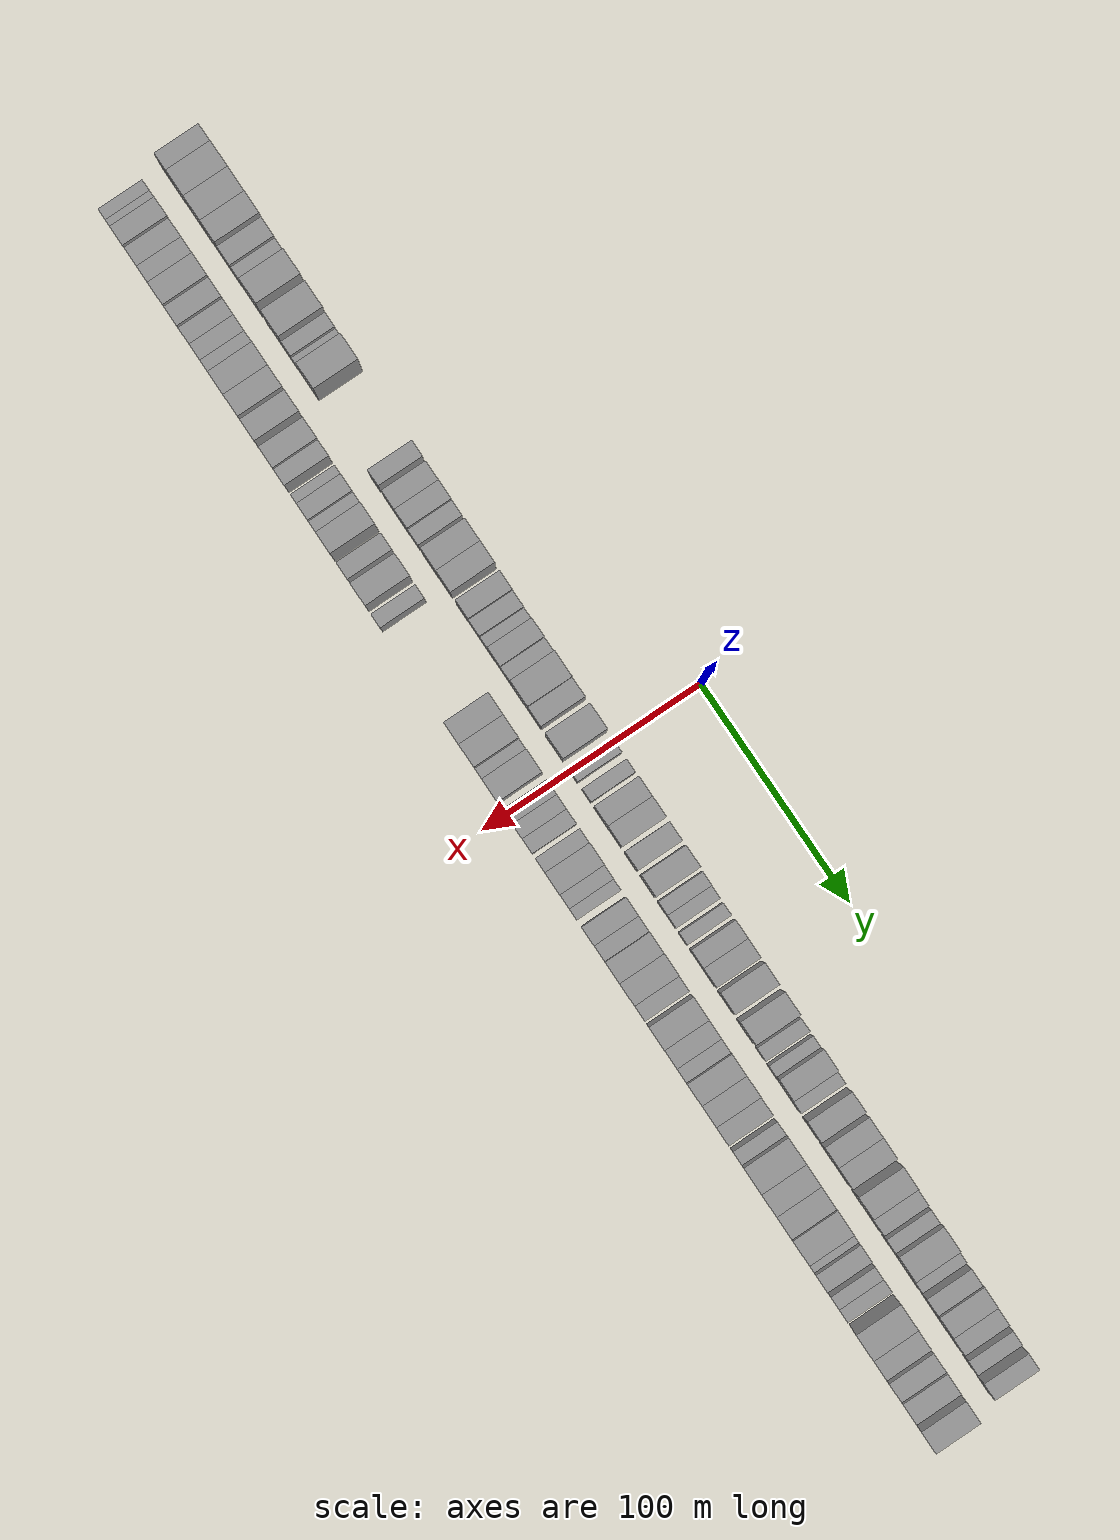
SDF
<sdf version="1.6">
 <world name="default">
  <scene>
   <sky><clouds><speed>12</speed></clouds></sky>
   <ambient>0.4 0.4 0.4 1</ambient>
   <background>0.7 0.7 0.7 1</background>
   <shadows>1</shadows>
  </scene>
  <gravity>0 0 -9.8066</gravity>
  <magnetic_field>6e-06 2.3e-05 -4.2e-05</magnetic_field>
  <physics default="0" name="default_physics" type="ode">
   <ode>
    <solver>
     <type>quick</type>
     <iters>10</iters>
     <sor>1.0</sor>
     <use_dynamic_moi_rescaling>0</use_dynamic_moi_rescaling>
    </solver>
    <constraints>
     <cfm>0</cfm>
     <erp>0.2</erp>
     <contact_max_correcting_vel>100</contact_max_correcting_vel>
     <contact_surface_layer>0.001</contact_surface_layer>
    </constraints>
   </ode>
   <max_step_size>0.004</max_step_size>
   <real_time_factor>1</real_time_factor>
   <real_time_update_rate>250</real_time_update_rate>
  </physics>
  <light name="sun" type="directional">
   <pose>0 0 10 0 0 0</pose>
   <diffuse>0.8 0.8 0.8 1</diffuse>
   <specular>0.2 0.2 0.2 1</specular>
   <attenuation>
    <range>1000</range>
    <constant>0.9</constant>
    <linear>0.01</linear>
    <quadratic>0.001</quadratic>
   </attenuation>
   <direction>-0.5 0.1 -0.9</direction>
  </light>
  <model name="building_1">
   <static>1</static>
   <pose>50.0000 -273.6800 0 0.000000 0.000000 0.000000</pose>
   <link name="link">
    <pose>0 0 10.50 0 0 0</pose>
    <collision name="collision"><geometry><box><size>20.0000 8.6399 21.0000</size></box></geometry></collision>
    <visual name="visual">
     <cast_shadows>0</cast_shadows>
     <geometry><box><size>20.0000 8.6399 21.0000</size></box></geometry>
     <material>
      <script>
       <uri>model://grey_wall/materials/scripts</uri>
       <uri>model://grey_wall/materials/textures</uri>
       <name>vrc/grey_wall</name>
      </script>
     </material>
    </visual>
   </link>
  </model>
  <model name="building_2">
   <static>1</static>
   <pose>50.0000 -263.5427 0 0.000000 0.000000 0.000000</pose>
   <link name="link">
    <pose>0 0 12.00 0 0 0</pose>
    <collision name="collision"><geometry><box><size>20.0000 11.6347 24.0000</size></box></geometry></collision>
    <visual name="visual">
     <cast_shadows>0</cast_shadows>
     <geometry><box><size>20.0000 11.6347 24.0000</size></box></geometry>
     <material>
      <script>
       <uri>model://grey_wall/materials/scripts</uri>
       <uri>model://grey_wall/materials/textures</uri>
       <name>vrc/grey_wall</name>
      </script>
     </material>
    </visual>
   </link>
  </model>
  <model name="building_3">
   <static>1</static>
   <pose>50.0000 -252.1240 0 0.000000 0.000000 0.000000</pose>
   <link name="link">
    <pose>0 0 12.00 0 0 0</pose>
    <collision name="collision"><geometry><box><size>20.0000 11.2028 24.0000</size></box></geometry></collision>
    <visual name="visual">
     <cast_shadows>0</cast_shadows>
     <geometry><box><size>20.0000 11.2028 24.0000</size></box></geometry>
     <material>
      <script>
       <uri>model://grey_wall/materials/scripts</uri>
       <uri>model://grey_wall/materials/textures</uri>
       <name>vrc/grey_wall</name>
      </script>
     </material>
    </visual>
   </link>
  </model>
  <model name="building_4">
   <static>1</static>
   <pose>50.0000 -241.5626 0 0.000000 0.000000 0.000000</pose>
   <link name="link">
    <pose>0 0 12.00 0 0 0</pose>
    <collision name="collision"><geometry><box><size>20.0000 9.9202 24.0000</size></box></geometry></collision>
    <visual name="visual">
     <cast_shadows>0</cast_shadows>
     <geometry><box><size>20.0000 9.9202 24.0000</size></box></geometry>
     <material>
      <script>
       <uri>model://grey_wall/materials/scripts</uri>
       <uri>model://grey_wall/materials/textures</uri>
       <name>vrc/grey_wall</name>
      </script>
     </material>
    </visual>
   </link>
  </model>
  <model name="building_5">
   <static>1</static>
   <pose>50.0000 -232.2219 0 0.000000 0.000000 0.000000</pose>
   <link name="link">
    <pose>0 0 9.00 0 0 0</pose>
    <collision name="collision"><geometry><box><size>20.0000 8.7611 18.0000</size></box></geometry></collision>
    <visual name="visual">
     <cast_shadows>0</cast_shadows>
     <geometry><box><size>20.0000 8.7611 18.0000</size></box></geometry>
     <material>
      <script>
       <uri>model://grey_wall/materials/scripts</uri>
       <uri>model://grey_wall/materials/textures</uri>
       <name>vrc/grey_wall</name>
      </script>
     </material>
    </visual>
   </link>
  </model>
  <model name="building_6">
   <static>1</static>
   <pose>50.0000 -224.1485 0 0.000000 0.000000 0.000000</pose>
   <link name="link">
    <pose>0 0 7.50 0 0 0</pose>
    <collision name="collision"><geometry><box><size>20.0000 7.3857 15.0000</size></box></geometry></collision>
    <visual name="visual">
     <cast_shadows>0</cast_shadows>
     <geometry><box><size>20.0000 7.3857 15.0000</size></box></geometry>
     <material>
      <script>
       <uri>model://grey_wall/materials/scripts</uri>
       <uri>model://grey_wall/materials/textures</uri>
       <name>vrc/grey_wall</name>
      </script>
     </material>
    </visual>
   </link>
  </model>
  <model name="building_7">
   <static>1</static>
   <pose>50.0000 -214.6706 0 0.000000 0.000000 0.000000</pose>
   <link name="link">
    <pose>0 0 12.00 0 0 0</pose>
    <collision name="collision"><geometry><box><size>20.0000 11.5701 24.0000</size></box></geometry></collision>
    <visual name="visual">
     <cast_shadows>0</cast_shadows>
     <geometry><box><size>20.0000 11.5701 24.0000</size></box></geometry>
     <material>
      <script>
       <uri>model://grey_wall/materials/scripts</uri>
       <uri>model://grey_wall/materials/textures</uri>
       <name>vrc/grey_wall</name>
      </script>
     </material>
    </visual>
   </link>
  </model>
  <model name="building_8">
   <static>1</static>
   <pose>50.0000 -199.9398 0 0.000000 0.000000 0.000000</pose>
   <link name="link">
    <pose>0 0 12.00 0 0 0</pose>
    <collision name="collision"><geometry><box><size>20.0000 11.8915 24.0000</size></box></geometry></collision>
    <visual name="visual">
     <cast_shadows>0</cast_shadows>
     <geometry><box><size>20.0000 11.8915 24.0000</size></box></geometry>
     <material>
      <script>
       <uri>model://grey_wall/materials/scripts</uri>
       <uri>model://grey_wall/materials/textures</uri>
       <name>vrc/grey_wall</name>
      </script>
     </material>
    </visual>
   </link>
  </model>
  <model name="building_9">
   <static>1</static>
   <pose>50.0000 -190.6809 0 0.000000 0.000000 0.000000</pose>
   <link name="link">
    <pose>0 0 7.50 0 0 0</pose>
    <collision name="collision"><geometry><box><size>20.0000 6.6264 15.0000</size></box></geometry></collision>
    <visual name="visual">
     <cast_shadows>0</cast_shadows>
     <geometry><box><size>20.0000 6.6264 15.0000</size></box></geometry>
     <material>
      <script>
       <uri>model://grey_wall/materials/scripts</uri>
       <uri>model://grey_wall/materials/textures</uri>
       <name>vrc/grey_wall</name>
      </script>
     </material>
    </visual>
   </link>
  </model>
  <model name="building_10">
   <static>1</static>
   <pose>50.0000 -184.7908 0 0.000000 0.000000 0.000000</pose>
   <link name="link">
    <pose>0 0 6.00 0 0 0</pose>
    <collision name="collision"><geometry><box><size>20.0000 5.1538 12.0000</size></box></geometry></collision>
    <visual name="visual">
     <cast_shadows>0</cast_shadows>
     <geometry><box><size>20.0000 5.1538 12.0000</size></box></geometry>
     <material>
      <script>
       <uri>model://grey_wall/materials/scripts</uri>
       <uri>model://grey_wall/materials/textures</uri>
       <name>vrc/grey_wall</name>
      </script>
     </material>
    </visual>
   </link>
  </model>
  <model name="building_11">
   <static>1</static>
   <pose>50.0000 -176.3409 0 0.000000 0.000000 0.000000</pose>
   <link name="link">
    <pose>0 0 12.00 0 0 0</pose>
    <collision name="collision"><geometry><box><size>20.0000 11.7459 24.0000</size></box></geometry></collision>
    <visual name="visual">
     <cast_shadows>0</cast_shadows>
     <geometry><box><size>20.0000 11.7459 24.0000</size></box></geometry>
     <material>
      <script>
       <uri>model://grey_wall/materials/scripts</uri>
       <uri>model://grey_wall/materials/textures</uri>
       <name>vrc/grey_wall</name>
      </script>
     </material>
    </visual>
   </link>
  </model>
  <model name="building_12">
   <static>1</static>
   <pose>50.0000 -131.5599 0 0.000000 0.000000 0.000000</pose>
   <link name="link">
    <pose>0 0 9.00 0 0 0</pose>
    <collision name="collision"><geometry><box><size>20.0000 7.2720 18.0000</size></box></geometry></collision>
    <visual name="visual">
     <cast_shadows>0</cast_shadows>
     <geometry><box><size>20.0000 7.2720 18.0000</size></box></geometry>
     <material>
      <script>
       <uri>model://grey_wall/materials/scripts</uri>
       <uri>model://grey_wall/materials/textures</uri>
       <name>vrc/grey_wall</name>
      </script>
     </material>
    </visual>
   </link>
  </model>
  <model name="building_13">
   <static>1</static>
   <pose>50.0000 -121.6003 0 0.000000 0.000000 0.000000</pose>
   <link name="link">
    <pose>0 0 9.00 0 0 0</pose>
    <collision name="collision"><geometry><box><size>20.0000 8.6473 18.0000</size></box></geometry></collision>
    <visual name="visual">
     <cast_shadows>0</cast_shadows>
     <geometry><box><size>20.0000 8.6473 18.0000</size></box></geometry>
     <material>
      <script>
       <uri>model://grey_wall/materials/scripts</uri>
       <uri>model://grey_wall/materials/textures</uri>
       <name>vrc/grey_wall</name>
      </script>
     </material>
    </visual>
   </link>
  </model>
  <model name="building_14">
   <static>1</static>
   <pose>50.0000 -112.9664 0 0.000000 0.000000 0.000000</pose>
   <link name="link">
    <pose>0 0 9.00 0 0 0</pose>
    <collision name="collision"><geometry><box><size>20.0000 8.6204 18.0000</size></box></geometry></collision>
    <visual name="visual">
     <cast_shadows>0</cast_shadows>
     <geometry><box><size>20.0000 8.6204 18.0000</size></box></geometry>
     <material>
      <script>
       <uri>model://grey_wall/materials/scripts</uri>
       <uri>model://grey_wall/materials/textures</uri>
       <name>vrc/grey_wall</name>
      </script>
     </material>
    </visual>
   </link>
  </model>
  <model name="building_15">
   <static>1</static>
   <pose>50.0000 -105.1115 0 0.000000 0.000000 0.000000</pose>
   <link name="link">
    <pose>0 0 7.50 0 0 0</pose>
    <collision name="collision"><geometry><box><size>20.0000 7.0894 15.0000</size></box></geometry></collision>
    <visual name="visual">
     <cast_shadows>0</cast_shadows>
     <geometry><box><size>20.0000 7.0894 15.0000</size></box></geometry>
     <material>
      <script>
       <uri>model://grey_wall/materials/scripts</uri>
       <uri>model://grey_wall/materials/textures</uri>
       <name>vrc/grey_wall</name>
      </script>
     </material>
    </visual>
   </link>
  </model>
  <model name="building_16">
   <static>1</static>
   <pose>50.0000 -94.4157 0 0.000000 0.000000 0.000000</pose>
   <link name="link">
    <pose>0 0 10.50 0 0 0</pose>
    <collision name="collision"><geometry><box><size>20.0000 10.3022 21.0000</size></box></geometry></collision>
    <visual name="visual">
     <cast_shadows>0</cast_shadows>
     <geometry><box><size>20.0000 10.3022 21.0000</size></box></geometry>
     <material>
      <script>
       <uri>model://grey_wall/materials/scripts</uri>
       <uri>model://grey_wall/materials/textures</uri>
       <name>vrc/grey_wall</name>
      </script>
     </material>
    </visual>
   </link>
  </model>
  <model name="building_17">
   <static>1</static>
   <pose>50.0000 -84.3508 0 0.000000 0.000000 0.000000</pose>
   <link name="link">
    <pose>0 0 10.50 0 0 0</pose>
    <collision name="collision"><geometry><box><size>20.0000 9.8277 21.0000</size></box></geometry></collision>
    <visual name="visual">
     <cast_shadows>0</cast_shadows>
     <geometry><box><size>20.0000 9.8277 21.0000</size></box></geometry>
     <material>
      <script>
       <uri>model://grey_wall/materials/scripts</uri>
       <uri>model://grey_wall/materials/textures</uri>
       <name>vrc/grey_wall</name>
      </script>
     </material>
    </visual>
   </link>
  </model>
  <model name="building_18">
   <static>1</static>
   <pose>50.0000 -72.1331 0 0.000000 0.000000 0.000000</pose>
   <link name="link">
    <pose>0 0 9.00 0 0 0</pose>
    <collision name="collision"><geometry><box><size>20.0000 8.6077 18.0000</size></box></geometry></collision>
    <visual name="visual">
     <cast_shadows>0</cast_shadows>
     <geometry><box><size>20.0000 8.6077 18.0000</size></box></geometry>
     <material>
      <script>
       <uri>model://grey_wall/materials/scripts</uri>
       <uri>model://grey_wall/materials/textures</uri>
       <name>vrc/grey_wall</name>
      </script>
     </material>
    </visual>
   </link>
  </model>
  <model name="building_19">
   <static>1</static>
   <pose>50.0000 -64.0873 0 0.000000 0.000000 0.000000</pose>
   <link name="link">
    <pose>0 0 7.50 0 0 0</pose>
    <collision name="collision"><geometry><box><size>20.0000 7.4838 15.0000</size></box></geometry></collision>
    <visual name="visual">
     <cast_shadows>0</cast_shadows>
     <geometry><box><size>20.0000 7.4838 15.0000</size></box></geometry>
     <material>
      <script>
       <uri>model://grey_wall/materials/scripts</uri>
       <uri>model://grey_wall/materials/textures</uri>
       <name>vrc/grey_wall</name>
      </script>
     </material>
    </visual>
   </link>
  </model>
  <model name="building_20">
   <static>1</static>
   <pose>50.0000 -57.7232 0 0.000000 0.000000 0.000000</pose>
   <link name="link">
    <pose>0 0 6.00 0 0 0</pose>
    <collision name="collision"><geometry><box><size>20.0000 5.2445 12.0000</size></box></geometry></collision>
    <visual name="visual">
     <cast_shadows>0</cast_shadows>
     <geometry><box><size>20.0000 5.2445 12.0000</size></box></geometry>
     <material>
      <script>
       <uri>model://grey_wall/materials/scripts</uri>
       <uri>model://grey_wall/materials/textures</uri>
       <name>vrc/grey_wall</name>
      </script>
     </material>
    </visual>
   </link>
  </model>
  <model name="building_21">
   <static>1</static>
   <pose>50.0000 -50.7852 0 0.000000 0.000000 0.000000</pose>
   <link name="link">
    <pose>0 0 9.00 0 0 0</pose>
    <collision name="collision"><geometry><box><size>20.0000 8.6315 18.0000</size></box></geometry></collision>
    <visual name="visual">
     <cast_shadows>0</cast_shadows>
     <geometry><box><size>20.0000 8.6315 18.0000</size></box></geometry>
     <material>
      <script>
       <uri>model://grey_wall/materials/scripts</uri>
       <uri>model://grey_wall/materials/textures</uri>
       <name>vrc/grey_wall</name>
      </script>
     </material>
    </visual>
   </link>
  </model>
  <model name="building_22">
   <static>1</static>
   <pose>50.0000 -43.0799 0 0.000000 0.000000 0.000000</pose>
   <link name="link">
    <pose>0 0 7.50 0 0 0</pose>
    <collision name="collision"><geometry><box><size>20.0000 6.7789 15.0000</size></box></geometry></collision>
    <visual name="visual">
     <cast_shadows>0</cast_shadows>
     <geometry><box><size>20.0000 6.7789 15.0000</size></box></geometry>
     <material>
      <script>
       <uri>model://grey_wall/materials/scripts</uri>
       <uri>model://grey_wall/materials/textures</uri>
       <name>vrc/grey_wall</name>
      </script>
     </material>
    </visual>
   </link>
  </model>
  <model name="building_23">
   <static>1</static>
   <pose>50.0000 -33.8264 0 0.000000 0.000000 0.000000</pose>
   <link name="link">
    <pose>0 0 12.00 0 0 0</pose>
    <collision name="collision"><geometry><box><size>20.0000 11.7282 24.0000</size></box></geometry></collision>
    <visual name="visual">
     <cast_shadows>0</cast_shadows>
     <geometry><box><size>20.0000 11.7282 24.0000</size></box></geometry>
     <material>
      <script>
       <uri>model://grey_wall/materials/scripts</uri>
       <uri>model://grey_wall/materials/textures</uri>
       <name>vrc/grey_wall</name>
      </script>
     </material>
    </visual>
   </link>
  </model>
  <model name="building_24">
   <static>1</static>
   <pose>50.0000 -23.6046 0 0.000000 0.000000 0.000000</pose>
   <link name="link">
    <pose>0 0 10.50 0 0 0</pose>
    <collision name="collision"><geometry><box><size>20.0000 8.7154 21.0000</size></box></geometry></collision>
    <visual name="visual">
     <cast_shadows>0</cast_shadows>
     <geometry><box><size>20.0000 8.7154 21.0000</size></box></geometry>
     <material>
      <script>
       <uri>model://grey_wall/materials/scripts</uri>
       <uri>model://grey_wall/materials/textures</uri>
       <name>vrc/grey_wall</name>
      </script>
     </material>
    </visual>
   </link>
  </model>
  <model name="building_25">
   <static>1</static>
   <pose>50.0000 -10.4218 0 0.000000 0.000000 0.000000</pose>
   <link name="link">
    <pose>0 0 12.00 0 0 0</pose>
    <collision name="collision"><geometry><box><size>20.0000 11.6502 24.0000</size></box></geometry></collision>
    <visual name="visual">
     <cast_shadows>0</cast_shadows>
     <geometry><box><size>20.0000 11.6502 24.0000</size></box></geometry>
     <material>
      <script>
       <uri>model://grey_wall/materials/scripts</uri>
       <uri>model://grey_wall/materials/textures</uri>
       <name>vrc/grey_wall</name>
      </script>
     </material>
    </visual>
   </link>
  </model>
  <model name="building_26">
   <static>1</static>
   <pose>50.0000 1.8205 0 0.000000 0.000000 0.000000</pose>
   <link name="link">
    <pose>0 0 7.50 0 0 0</pose>
    <collision name="collision"><geometry><box><size>20.0000 6.8344 15.0000</size></box></geometry></collision>
    <visual name="visual">
     <cast_shadows>0</cast_shadows>
     <geometry><box><size>20.0000 6.8344 15.0000</size></box></geometry>
     <material>
      <script>
       <uri>model://grey_wall/materials/scripts</uri>
       <uri>model://grey_wall/materials/textures</uri>
       <name>vrc/grey_wall</name>
      </script>
     </material>
    </visual>
   </link>
  </model>
  <model name="building_27">
   <static>1</static>
   <pose>50.0000 11.2494 0 0.000000 0.000000 0.000000</pose>
   <link name="link">
    <pose>0 0 7.50 0 0 0</pose>
    <collision name="collision"><geometry><box><size>20.0000 6.0233 15.0000</size></box></geometry></collision>
    <visual name="visual">
     <cast_shadows>0</cast_shadows>
     <geometry><box><size>20.0000 6.0233 15.0000</size></box></geometry>
     <material>
      <script>
       <uri>model://grey_wall/materials/scripts</uri>
       <uri>model://grey_wall/materials/textures</uri>
       <name>vrc/grey_wall</name>
      </script>
     </material>
    </visual>
   </link>
  </model>
  <model name="building_28">
   <static>1</static>
   <pose>50.0000 20.7345 0 0.000000 0.000000 0.000000</pose>
   <link name="link">
    <pose>0 0 10.50 0 0 0</pose>
    <collision name="collision"><geometry><box><size>20.0000 8.9469 21.0000</size></box></geometry></collision>
    <visual name="visual">
     <cast_shadows>0</cast_shadows>
     <geometry><box><size>20.0000 8.9469 21.0000</size></box></geometry>
     <material>
      <script>
       <uri>model://grey_wall/materials/scripts</uri>
       <uri>model://grey_wall/materials/textures</uri>
       <name>vrc/grey_wall</name>
      </script>
     </material>
    </visual>
   </link>
  </model>
  <model name="building_29">
   <static>1</static>
   <pose>50.0000 29.8914 0 0.000000 0.000000 0.000000</pose>
   <link name="link">
    <pose>0 0 10.50 0 0 0</pose>
    <collision name="collision"><geometry><box><size>20.0000 9.3669 21.0000</size></box></geometry></collision>
    <visual name="visual">
     <cast_shadows>0</cast_shadows>
     <geometry><box><size>20.0000 9.3669 21.0000</size></box></geometry>
     <material>
      <script>
       <uri>model://grey_wall/materials/scripts</uri>
       <uri>model://grey_wall/materials/textures</uri>
       <name>vrc/grey_wall</name>
      </script>
     </material>
    </visual>
   </link>
  </model>
  <model name="building_30">
   <static>1</static>
   <pose>50.0000 40.8445 0 0.000000 0.000000 0.000000</pose>
   <link name="link">
    <pose>0 0 10.50 0 0 0</pose>
    <collision name="collision"><geometry><box><size>20.0000 8.5393 21.0000</size></box></geometry></collision>
    <visual name="visual">
     <cast_shadows>0</cast_shadows>
     <geometry><box><size>20.0000 8.5393 21.0000</size></box></geometry>
     <material>
      <script>
       <uri>model://grey_wall/materials/scripts</uri>
       <uri>model://grey_wall/materials/textures</uri>
       <name>vrc/grey_wall</name>
      </script>
     </material>
    </visual>
   </link>
  </model>
  <model name="building_31">
   <static>1</static>
   <pose>50.0000 52.0060 0 0.000000 0.000000 0.000000</pose>
   <link name="link">
    <pose>0 0 12.00 0 0 0</pose>
    <collision name="collision"><geometry><box><size>20.0000 9.7837 24.0000</size></box></geometry></collision>
    <visual name="visual">
     <cast_shadows>0</cast_shadows>
     <geometry><box><size>20.0000 9.7837 24.0000</size></box></geometry>
     <material>
      <script>
       <uri>model://grey_wall/materials/scripts</uri>
       <uri>model://grey_wall/materials/textures</uri>
       <name>vrc/grey_wall</name>
      </script>
     </material>
    </visual>
   </link>
  </model>
  <model name="building_32">
   <static>1</static>
   <pose>50.0000 62.0029 0 0.000000 0.000000 0.000000</pose>
   <link name="link">
    <pose>0 0 7.50 0 0 0</pose>
    <collision name="collision"><geometry><box><size>20.0000 6.2100 15.0000</size></box></geometry></collision>
    <visual name="visual">
     <cast_shadows>0</cast_shadows>
     <geometry><box><size>20.0000 6.2100 15.0000</size></box></geometry>
     <material>
      <script>
       <uri>model://grey_wall/materials/scripts</uri>
       <uri>model://grey_wall/materials/textures</uri>
       <name>vrc/grey_wall</name>
      </script>
     </material>
    </visual>
   </link>
  </model>
  <model name="building_33">
   <static>1</static>
   <pose>50.0000 68.0399 0 0.000000 0.000000 0.000000</pose>
   <link name="link">
    <pose>0 0 6.00 0 0 0</pose>
    <collision name="collision"><geometry><box><size>20.0000 5.8642 12.0000</size></box></geometry></collision>
    <visual name="visual">
     <cast_shadows>0</cast_shadows>
     <geometry><box><size>20.0000 5.8642 12.0000</size></box></geometry>
     <material>
      <script>
       <uri>model://grey_wall/materials/scripts</uri>
       <uri>model://grey_wall/materials/textures</uri>
       <name>vrc/grey_wall</name>
      </script>
     </material>
    </visual>
   </link>
  </model>
  <model name="building_34">
   <static>1</static>
   <pose>50.0000 75.7531 0 0.000000 0.000000 0.000000</pose>
   <link name="link">
    <pose>0 0 6.00 0 0 0</pose>
    <collision name="collision"><geometry><box><size>20.0000 5.5622 12.0000</size></box></geometry></collision>
    <visual name="visual">
     <cast_shadows>0</cast_shadows>
     <geometry><box><size>20.0000 5.5622 12.0000</size></box></geometry>
     <material>
      <script>
       <uri>model://grey_wall/materials/scripts</uri>
       <uri>model://grey_wall/materials/textures</uri>
       <name>vrc/grey_wall</name>
      </script>
     </material>
    </visual>
   </link>
  </model>
  <model name="building_35">
   <static>1</static>
   <pose>50.0000 84.6452 0 0.000000 0.000000 0.000000</pose>
   <link name="link">
    <pose>0 0 9.00 0 0 0</pose>
    <collision name="collision"><geometry><box><size>20.0000 8.2221 18.0000</size></box></geometry></collision>
    <visual name="visual">
     <cast_shadows>0</cast_shadows>
     <geometry><box><size>20.0000 8.2221 18.0000</size></box></geometry>
     <material>
      <script>
       <uri>model://grey_wall/materials/scripts</uri>
       <uri>model://grey_wall/materials/textures</uri>
       <name>vrc/grey_wall</name>
      </script>
     </material>
    </visual>
   </link>
  </model>
  <model name="building_36">
   <static>1</static>
   <pose>50.0000 93.0902 0 0.000000 0.000000 0.000000</pose>
   <link name="link">
    <pose>0 0 9.00 0 0 0</pose>
    <collision name="collision"><geometry><box><size>20.0000 8.6678 18.0000</size></box></geometry></collision>
    <visual name="visual">
     <cast_shadows>0</cast_shadows>
     <geometry><box><size>20.0000 8.6678 18.0000</size></box></geometry>
     <material>
      <script>
       <uri>model://grey_wall/materials/scripts</uri>
       <uri>model://grey_wall/materials/textures</uri>
       <name>vrc/grey_wall</name>
      </script>
     </material>
    </visual>
   </link>
  </model>
  <model name="building_37">
   <static>1</static>
   <pose>50.0000 104.3511 0 0.000000 0.000000 0.000000</pose>
   <link name="link">
    <pose>0 0 10.50 0 0 0</pose>
    <collision name="collision"><geometry><box><size>20.0000 9.8541 21.0000</size></box></geometry></collision>
    <visual name="visual">
     <cast_shadows>0</cast_shadows>
     <geometry><box><size>20.0000 9.8541 21.0000</size></box></geometry>
     <material>
      <script>
       <uri>model://grey_wall/materials/scripts</uri>
       <uri>model://grey_wall/materials/textures</uri>
       <name>vrc/grey_wall</name>
      </script>
     </material>
    </visual>
   </link>
  </model>
  <model name="building_38">
   <static>1</static>
   <pose>50.0000 117.4707 0 0.000000 0.000000 0.000000</pose>
   <link name="link">
    <pose>0 0 12.00 0 0 0</pose>
    <collision name="collision"><geometry><box><size>20.0000 10.3851 24.0000</size></box></geometry></collision>
    <visual name="visual">
     <cast_shadows>0</cast_shadows>
     <geometry><box><size>20.0000 10.3851 24.0000</size></box></geometry>
     <material>
      <script>
       <uri>model://grey_wall/materials/scripts</uri>
       <uri>model://grey_wall/materials/textures</uri>
       <name>vrc/grey_wall</name>
      </script>
     </material>
    </visual>
   </link>
  </model>
  <model name="building_39">
   <static>1</static>
   <pose>50.0000 127.6565 0 0.000000 0.000000 0.000000</pose>
   <link name="link">
    <pose>0 0 6.00 0 0 0</pose>
    <collision name="collision"><geometry><box><size>20.0000 5.9864 12.0000</size></box></geometry></collision>
    <visual name="visual">
     <cast_shadows>0</cast_shadows>
     <geometry><box><size>20.0000 5.9864 12.0000</size></box></geometry>
     <material>
      <script>
       <uri>model://grey_wall/materials/scripts</uri>
       <uri>model://grey_wall/materials/textures</uri>
       <name>vrc/grey_wall</name>
      </script>
     </material>
    </visual>
   </link>
  </model>
  <model name="building_40">
   <static>1</static>
   <pose>50.0000 135.1891 0 0.000000 0.000000 0.000000</pose>
   <link name="link">
    <pose>0 0 6.00 0 0 0</pose>
    <collision name="collision"><geometry><box><size>20.0000 5.0788 12.0000</size></box></geometry></collision>
    <visual name="visual">
     <cast_shadows>0</cast_shadows>
     <geometry><box><size>20.0000 5.0788 12.0000</size></box></geometry>
     <material>
      <script>
       <uri>model://grey_wall/materials/scripts</uri>
       <uri>model://grey_wall/materials/textures</uri>
       <name>vrc/grey_wall</name>
      </script>
     </material>
    </visual>
   </link>
  </model>
  <model name="building_41">
   <static>1</static>
   <pose>50.0000 142.5829 0 0.000000 0.000000 0.000000</pose>
   <link name="link">
    <pose>0 0 12.00 0 0 0</pose>
    <collision name="collision"><geometry><box><size>20.0000 9.7087 24.0000</size></box></geometry></collision>
    <visual name="visual">
     <cast_shadows>0</cast_shadows>
     <geometry><box><size>20.0000 9.7087 24.0000</size></box></geometry>
     <material>
      <script>
       <uri>model://grey_wall/materials/scripts</uri>
       <uri>model://grey_wall/materials/textures</uri>
       <name>vrc/grey_wall</name>
      </script>
     </material>
    </visual>
   </link>
  </model>
  <model name="building_42">
   <static>1</static>
   <pose>50.0000 150.5750 0 0.000000 0.000000 0.000000</pose>
   <link name="link">
    <pose>0 0 7.50 0 0 0</pose>
    <collision name="collision"><geometry><box><size>20.0000 6.2755 15.0000</size></box></geometry></collision>
    <visual name="visual">
     <cast_shadows>0</cast_shadows>
     <geometry><box><size>20.0000 6.2755 15.0000</size></box></geometry>
     <material>
      <script>
       <uri>model://grey_wall/materials/scripts</uri>
       <uri>model://grey_wall/materials/textures</uri>
       <name>vrc/grey_wall</name>
      </script>
     </material>
    </visual>
   </link>
  </model>
  <model name="building_43">
   <static>1</static>
   <pose>50.0000 161.3893 0 0.000000 0.000000 0.000000</pose>
   <link name="link">
    <pose>0 0 10.50 0 0 0</pose>
    <collision name="collision"><geometry><box><size>20.0000 9.3530 21.0000</size></box></geometry></collision>
    <visual name="visual">
     <cast_shadows>0</cast_shadows>
     <geometry><box><size>20.0000 9.3530 21.0000</size></box></geometry>
     <material>
      <script>
       <uri>model://grey_wall/materials/scripts</uri>
       <uri>model://grey_wall/materials/textures</uri>
       <name>vrc/grey_wall</name>
      </script>
     </material>
    </visual>
   </link>
  </model>
  <model name="building_44">
   <static>1</static>
   <pose>50.0000 172.6418 0 0.000000 0.000000 0.000000</pose>
   <link name="link">
    <pose>0 0 10.50 0 0 0</pose>
    <collision name="collision"><geometry><box><size>20.0000 9.1519 21.0000</size></box></geometry></collision>
    <visual name="visual">
     <cast_shadows>0</cast_shadows>
     <geometry><box><size>20.0000 9.1519 21.0000</size></box></geometry>
     <material>
      <script>
       <uri>model://grey_wall/materials/scripts</uri>
       <uri>model://grey_wall/materials/textures</uri>
       <name>vrc/grey_wall</name>
      </script>
     </material>
    </visual>
   </link>
  </model>
  <model name="building_45">
   <static>1</static>
   <pose>50.0000 181.9370 0 0.000000 0.000000 0.000000</pose>
   <link name="link">
    <pose>0 0 10.50 0 0 0</pose>
    <collision name="collision"><geometry><box><size>20.0000 9.4385 21.0000</size></box></geometry></collision>
    <visual name="visual">
     <cast_shadows>0</cast_shadows>
     <geometry><box><size>20.0000 9.4385 21.0000</size></box></geometry>
     <material>
      <script>
       <uri>model://grey_wall/materials/scripts</uri>
       <uri>model://grey_wall/materials/textures</uri>
       <name>vrc/grey_wall</name>
      </script>
     </material>
    </visual>
   </link>
  </model>
  <model name="building_46">
   <static>1</static>
   <pose>50.0000 194.6223 0 0.000000 0.000000 0.000000</pose>
   <link name="link">
    <pose>0 0 12.00 0 0 0</pose>
    <collision name="collision"><geometry><box><size>20.0000 9.9322 24.0000</size></box></geometry></collision>
    <visual name="visual">
     <cast_shadows>0</cast_shadows>
     <geometry><box><size>20.0000 9.9322 24.0000</size></box></geometry>
     <material>
      <script>
       <uri>model://grey_wall/materials/scripts</uri>
       <uri>model://grey_wall/materials/textures</uri>
       <name>vrc/grey_wall</name>
      </script>
     </material>
    </visual>
   </link>
  </model>
  <model name="building_47">
   <static>1</static>
   <pose>50.0000 203.6791 0 0.000000 0.000000 0.000000</pose>
   <link name="link">
    <pose>0 0 9.00 0 0 0</pose>
    <collision name="collision"><geometry><box><size>20.0000 8.1814 18.0000</size></box></geometry></collision>
    <visual name="visual">
     <cast_shadows>0</cast_shadows>
     <geometry><box><size>20.0000 8.1814 18.0000</size></box></geometry>
     <material>
      <script>
       <uri>model://grey_wall/materials/scripts</uri>
       <uri>model://grey_wall/materials/textures</uri>
       <name>vrc/grey_wall</name>
      </script>
     </material>
    </visual>
   </link>
  </model>
  <model name="building_48">
   <static>1</static>
   <pose>50.0000 212.8587 0 0.000000 0.000000 0.000000</pose>
   <link name="link">
    <pose>0 0 7.50 0 0 0</pose>
    <collision name="collision"><geometry><box><size>20.0000 6.1778 15.0000</size></box></geometry></collision>
    <visual name="visual">
     <cast_shadows>0</cast_shadows>
     <geometry><box><size>20.0000 6.1778 15.0000</size></box></geometry>
     <material>
      <script>
       <uri>model://grey_wall/materials/scripts</uri>
       <uri>model://grey_wall/materials/textures</uri>
       <name>vrc/grey_wall</name>
      </script>
     </material>
    </visual>
   </link>
  </model>
  <model name="building_49">
   <static>1</static>
   <pose>50.0000 221.5191 0 0.000000 0.000000 0.000000</pose>
   <link name="link">
    <pose>0 0 12.00 0 0 0</pose>
    <collision name="collision"><geometry><box><size>20.0000 11.1430 24.0000</size></box></geometry></collision>
    <visual name="visual">
     <cast_shadows>0</cast_shadows>
     <geometry><box><size>20.0000 11.1430 24.0000</size></box></geometry>
     <material>
      <script>
       <uri>model://grey_wall/materials/scripts</uri>
       <uri>model://grey_wall/materials/textures</uri>
       <name>vrc/grey_wall</name>
      </script>
     </material>
    </visual>
   </link>
  </model>
  <model name="building_50">
   <static>1</static>
   <pose>50.0000 230.3307 0 0.000000 0.000000 0.000000</pose>
   <link name="link">
    <pose>0 0 7.50 0 0 0</pose>
    <collision name="collision"><geometry><box><size>20.0000 6.4800 15.0000</size></box></geometry></collision>
    <visual name="visual">
     <cast_shadows>0</cast_shadows>
     <geometry><box><size>20.0000 6.4800 15.0000</size></box></geometry>
     <material>
      <script>
       <uri>model://grey_wall/materials/scripts</uri>
       <uri>model://grey_wall/materials/textures</uri>
       <name>vrc/grey_wall</name>
      </script>
     </material>
    </visual>
   </link>
  </model>
  <model name="building_51">
   <static>1</static>
   <pose>50.0000 239.3495 0 0.000000 0.000000 0.000000</pose>
   <link name="link">
    <pose>0 0 9.00 0 0 0</pose>
    <collision name="collision"><geometry><box><size>20.0000 7.5577 18.0000</size></box></geometry></collision>
    <visual name="visual">
     <cast_shadows>0</cast_shadows>
     <geometry><box><size>20.0000 7.5577 18.0000</size></box></geometry>
     <material>
      <script>
       <uri>model://grey_wall/materials/scripts</uri>
       <uri>model://grey_wall/materials/textures</uri>
       <name>vrc/grey_wall</name>
      </script>
     </material>
    </visual>
   </link>
  </model>
  <model name="building_52">
   <static>1</static>
   <pose>50.0000 247.7232 0 0.000000 0.000000 0.000000</pose>
   <link name="link">
    <pose>0 0 10.50 0 0 0</pose>
    <collision name="collision"><geometry><box><size>20.0000 9.1896 21.0000</size></box></geometry></collision>
    <visual name="visual">
     <cast_shadows>0</cast_shadows>
     <geometry><box><size>20.0000 9.1896 21.0000</size></box></geometry>
     <material>
      <script>
       <uri>model://grey_wall/materials/scripts</uri>
       <uri>model://grey_wall/materials/textures</uri>
       <name>vrc/grey_wall</name>
      </script>
     </material>
    </visual>
   </link>
  </model>
  <model name="building_53">
   <static>1</static>
   <pose>50.0000 256.4571 0 0.000000 0.000000 0.000000</pose>
   <link name="link">
    <pose>0 0 9.00 0 0 0</pose>
    <collision name="collision"><geometry><box><size>20.0000 8.2782 18.0000</size></box></geometry></collision>
    <visual name="visual">
     <cast_shadows>0</cast_shadows>
     <geometry><box><size>20.0000 8.2782 18.0000</size></box></geometry>
     <material>
      <script>
       <uri>model://grey_wall/materials/scripts</uri>
       <uri>model://grey_wall/materials/textures</uri>
       <name>vrc/grey_wall</name>
      </script>
     </material>
    </visual>
   </link>
  </model>
  <model name="building_54">
   <static>1</static>
   <pose>50.0000 266.7595 0 0.000000 0.000000 0.000000</pose>
   <link name="link">
    <pose>0 0 7.50 0 0 0</pose>
    <collision name="collision"><geometry><box><size>20.0000 6.3266 15.0000</size></box></geometry></collision>
    <visual name="visual">
     <cast_shadows>0</cast_shadows>
     <geometry><box><size>20.0000 6.3266 15.0000</size></box></geometry>
     <material>
      <script>
       <uri>model://grey_wall/materials/scripts</uri>
       <uri>model://grey_wall/materials/textures</uri>
       <name>vrc/grey_wall</name>
      </script>
     </material>
    </visual>
   </link>
  </model>
  <model name="building_55">
   <static>1</static>
   <pose>50.0000 276.5610 0 0.000000 0.000000 0.000000</pose>
   <link name="link">
    <pose>0 0 9.00 0 0 0</pose>
    <collision name="collision"><geometry><box><size>20.0000 7.2764 18.0000</size></box></geometry></collision>
    <visual name="visual">
     <cast_shadows>0</cast_shadows>
     <geometry><box><size>20.0000 7.2764 18.0000</size></box></geometry>
     <material>
      <script>
       <uri>model://grey_wall/materials/scripts</uri>
       <uri>model://grey_wall/materials/textures</uri>
       <name>vrc/grey_wall</name>
      </script>
     </material>
    </visual>
   </link>
  </model>
  <model name="building_56">
   <static>1</static>
   <pose>79.0000 -272.5074 0 0.000000 0.000000 0.000000</pose>
   <link name="link">
    <pose>0 0 6.00 0 0 0</pose>
    <collision name="collision"><geometry><box><size>20.0000 4.9853 12.0000</size></box></geometry></collision>
    <visual name="visual">
     <cast_shadows>0</cast_shadows>
     <geometry><box><size>20.0000 4.9853 12.0000</size></box></geometry>
     <material>
      <script>
       <uri>model://grey_wall/materials/scripts</uri>
       <uri>model://grey_wall/materials/textures</uri>
       <name>vrc/grey_wall</name>
      </script>
     </material>
    </visual>
   </link>
  </model>
  <model name="building_57">
   <static>1</static>
   <pose>79.0000 -267.1416 0 0.000000 0.000000 0.000000</pose>
   <link name="link">
    <pose>0 0 6.00 0 0 0</pose>
    <collision name="collision"><geometry><box><size>20.0000 5.7462 12.0000</size></box></geometry></collision>
    <visual name="visual">
     <cast_shadows>0</cast_shadows>
     <geometry><box><size>20.0000 5.7462 12.0000</size></box></geometry>
     <material>
      <script>
       <uri>model://grey_wall/materials/scripts</uri>
       <uri>model://grey_wall/materials/textures</uri>
       <name>vrc/grey_wall</name>
      </script>
     </material>
    </visual>
   </link>
  </model>
  <model name="building_58">
   <static>1</static>
   <pose>79.0000 -259.9325 0 0.000000 0.000000 0.000000</pose>
   <link name="link">
    <pose>0 0 10.50 0 0 0</pose>
    <collision name="collision"><geometry><box><size>20.0000 8.6721 21.0000</size></box></geometry></collision>
    <visual name="visual">
     <cast_shadows>0</cast_shadows>
     <geometry><box><size>20.0000 8.6721 21.0000</size></box></geometry>
     <material>
      <script>
       <uri>model://grey_wall/materials/scripts</uri>
       <uri>model://grey_wall/materials/textures</uri>
       <name>vrc/grey_wall</name>
      </script>
     </material>
    </visual>
   </link>
  </model>
  <model name="building_59">
   <static>1</static>
   <pose>79.0000 -251.3336 0 0.000000 0.000000 0.000000</pose>
   <link name="link">
    <pose>0 0 9.00 0 0 0</pose>
    <collision name="collision"><geometry><box><size>20.0000 8.5257 18.0000</size></box></geometry></collision>
    <visual name="visual">
     <cast_shadows>0</cast_shadows>
     <geometry><box><size>20.0000 8.5257 18.0000</size></box></geometry>
     <material>
      <script>
       <uri>model://grey_wall/materials/scripts</uri>
       <uri>model://grey_wall/materials/textures</uri>
       <name>vrc/grey_wall</name>
      </script>
     </material>
    </visual>
   </link>
  </model>
  <model name="building_60">
   <static>1</static>
   <pose>79.0000 -243.0124 0 0.000000 0.000000 0.000000</pose>
   <link name="link">
    <pose>0 0 9.00 0 0 0</pose>
    <collision name="collision"><geometry><box><size>20.0000 8.1168 18.0000</size></box></geometry></collision>
    <visual name="visual">
     <cast_shadows>0</cast_shadows>
     <geometry><box><size>20.0000 8.1168 18.0000</size></box></geometry>
     <material>
      <script>
       <uri>model://grey_wall/materials/scripts</uri>
       <uri>model://grey_wall/materials/textures</uri>
       <name>vrc/grey_wall</name>
      </script>
     </material>
    </visual>
   </link>
  </model>
  <model name="building_61">
   <static>1</static>
   <pose>79.0000 -233.8450 0 0.000000 0.000000 0.000000</pose>
   <link name="link">
    <pose>0 0 10.50 0 0 0</pose>
    <collision name="collision"><geometry><box><size>20.0000 10.2180 21.0000</size></box></geometry></collision>
    <visual name="visual">
     <cast_shadows>0</cast_shadows>
     <geometry><box><size>20.0000 10.2180 21.0000</size></box></geometry>
     <material>
      <script>
       <uri>model://grey_wall/materials/scripts</uri>
       <uri>model://grey_wall/materials/textures</uri>
       <name>vrc/grey_wall</name>
      </script>
     </material>
    </visual>
   </link>
  </model>
  <model name="building_62">
   <static>1</static>
   <pose>79.0000 -224.3165 0 0.000000 0.000000 0.000000</pose>
   <link name="link">
    <pose>0 0 9.00 0 0 0</pose>
    <collision name="collision"><geometry><box><size>20.0000 8.8390 18.0000</size></box></geometry></collision>
    <visual name="visual">
     <cast_shadows>0</cast_shadows>
     <geometry><box><size>20.0000 8.8390 18.0000</size></box></geometry>
     <material>
      <script>
       <uri>model://grey_wall/materials/scripts</uri>
       <uri>model://grey_wall/materials/textures</uri>
       <name>vrc/grey_wall</name>
      </script>
     </material>
    </visual>
   </link>
  </model>
  <model name="building_63">
   <static>1</static>
   <pose>79.0000 -216.1628 0 0.000000 0.000000 0.000000</pose>
   <link name="link">
    <pose>0 0 7.50 0 0 0</pose>
    <collision name="collision"><geometry><box><size>20.0000 7.4683 15.0000</size></box></geometry></collision>
    <visual name="visual">
     <cast_shadows>0</cast_shadows>
     <geometry><box><size>20.0000 7.4683 15.0000</size></box></geometry>
     <material>
      <script>
       <uri>model://grey_wall/materials/scripts</uri>
       <uri>model://grey_wall/materials/textures</uri>
       <name>vrc/grey_wall</name>
      </script>
     </material>
    </visual>
   </link>
  </model>
  <model name="building_64">
   <static>1</static>
   <pose>79.0000 -208.7522 0 0.000000 0.000000 0.000000</pose>
   <link name="link">
    <pose>0 0 7.50 0 0 0</pose>
    <collision name="collision"><geometry><box><size>20.0000 7.3530 15.0000</size></box></geometry></collision>
    <visual name="visual">
     <cast_shadows>0</cast_shadows>
     <geometry><box><size>20.0000 7.3530 15.0000</size></box></geometry>
     <material>
      <script>
       <uri>model://grey_wall/materials/scripts</uri>
       <uri>model://grey_wall/materials/textures</uri>
       <name>vrc/grey_wall</name>
      </script>
     </material>
    </visual>
   </link>
  </model>
  <model name="building_65">
   <static>1</static>
   <pose>79.0000 -201.8320 0 0.000000 0.000000 0.000000</pose>
   <link name="link">
    <pose>0 0 7.50 0 0 0</pose>
    <collision name="collision"><geometry><box><size>20.0000 6.4873 15.0000</size></box></geometry></collision>
    <visual name="visual">
     <cast_shadows>0</cast_shadows>
     <geometry><box><size>20.0000 6.4873 15.0000</size></box></geometry>
     <material>
      <script>
       <uri>model://grey_wall/materials/scripts</uri>
       <uri>model://grey_wall/materials/textures</uri>
       <name>vrc/grey_wall</name>
      </script>
     </material>
    </visual>
   </link>
  </model>
  <model name="building_66">
   <static>1</static>
   <pose>79.0000 -193.3451 0 0.000000 0.000000 0.000000</pose>
   <link name="link">
    <pose>0 0 10.50 0 0 0</pose>
    <collision name="collision"><geometry><box><size>20.0000 10.4865 21.0000</size></box></geometry></collision>
    <visual name="visual">
     <cast_shadows>0</cast_shadows>
     <geometry><box><size>20.0000 10.4865 21.0000</size></box></geometry>
     <material>
      <script>
       <uri>model://grey_wall/materials/scripts</uri>
       <uri>model://grey_wall/materials/textures</uri>
       <name>vrc/grey_wall</name>
      </script>
     </material>
    </visual>
   </link>
  </model>
  <model name="building_67">
   <static>1</static>
   <pose>79.0000 -183.1877 0 0.000000 0.000000 0.000000</pose>
   <link name="link">
    <pose>0 0 10.50 0 0 0</pose>
    <collision name="collision"><geometry><box><size>20.0000 9.8282 21.0000</size></box></geometry></collision>
    <visual name="visual">
     <cast_shadows>0</cast_shadows>
     <geometry><box><size>20.0000 9.8282 21.0000</size></box></geometry>
     <material>
      <script>
       <uri>model://grey_wall/materials/scripts</uri>
       <uri>model://grey_wall/materials/textures</uri>
       <name>vrc/grey_wall</name>
      </script>
     </material>
    </visual>
   </link>
  </model>
  <model name="building_68">
   <static>1</static>
   <pose>79.0000 -171.4203 0 0.000000 0.000000 0.000000</pose>
   <link name="link">
    <pose>0 0 12.00 0 0 0</pose>
    <collision name="collision"><geometry><box><size>20.0000 9.7066 24.0000</size></box></geometry></collision>
    <visual name="visual">
     <cast_shadows>0</cast_shadows>
     <geometry><box><size>20.0000 9.7066 24.0000</size></box></geometry>
     <material>
      <script>
       <uri>model://grey_wall/materials/scripts</uri>
       <uri>model://grey_wall/materials/textures</uri>
       <name>vrc/grey_wall</name>
      </script>
     </material>
    </visual>
   </link>
  </model>
  <model name="building_69">
   <static>1</static>
   <pose>79.0000 -159.7670 0 0.000000 0.000000 0.000000</pose>
   <link name="link">
    <pose>0 0 10.50 0 0 0</pose>
    <collision name="collision"><geometry><box><size>20.0000 9.6000 21.0000</size></box></geometry></collision>
    <visual name="visual">
     <cast_shadows>0</cast_shadows>
     <geometry><box><size>20.0000 9.6000 21.0000</size></box></geometry>
     <material>
      <script>
       <uri>model://grey_wall/materials/scripts</uri>
       <uri>model://grey_wall/materials/textures</uri>
       <name>vrc/grey_wall</name>
      </script>
     </material>
    </visual>
   </link>
  </model>
  <model name="building_70">
   <static>1</static>
   <pose>79.0000 -151.2891 0 0.000000 0.000000 0.000000</pose>
   <link name="link">
    <pose>0 0 9.00 0 0 0</pose>
    <collision name="collision"><geometry><box><size>20.0000 7.3558 18.0000</size></box></geometry></collision>
    <visual name="visual">
     <cast_shadows>0</cast_shadows>
     <geometry><box><size>20.0000 7.3558 18.0000</size></box></geometry>
     <material>
      <script>
       <uri>model://grey_wall/materials/scripts</uri>
       <uri>model://grey_wall/materials/textures</uri>
       <name>vrc/grey_wall</name>
      </script>
     </material>
    </visual>
   </link>
  </model>
  <model name="building_71">
   <static>1</static>
   <pose>79.0000 -142.0737 0 0.000000 0.000000 0.000000</pose>
   <link name="link">
    <pose>0 0 6.00 0 0 0</pose>
    <collision name="collision"><geometry><box><size>20.0000 5.0750 12.0000</size></box></geometry></collision>
    <visual name="visual">
     <cast_shadows>0</cast_shadows>
     <geometry><box><size>20.0000 5.0750 12.0000</size></box></geometry>
     <material>
      <script>
       <uri>model://grey_wall/materials/scripts</uri>
       <uri>model://grey_wall/materials/textures</uri>
       <name>vrc/grey_wall</name>
      </script>
     </material>
    </visual>
   </link>
  </model>
  <model name="building_72">
   <static>1</static>
   <pose>79.0000 -135.7143 0 0.000000 0.000000 0.000000</pose>
   <link name="link">
    <pose>0 0 9.00 0 0 0</pose>
    <collision name="collision"><geometry><box><size>20.0000 7.6437 18.0000</size></box></geometry></collision>
    <visual name="visual">
     <cast_shadows>0</cast_shadows>
     <geometry><box><size>20.0000 7.6437 18.0000</size></box></geometry>
     <material>
      <script>
       <uri>model://grey_wall/materials/scripts</uri>
       <uri>model://grey_wall/materials/textures</uri>
       <name>vrc/grey_wall</name>
      </script>
     </material>
    </visual>
   </link>
  </model>
  <model name="building_73">
   <static>1</static>
   <pose>79.0000 -128.7778 0 0.000000 0.000000 0.000000</pose>
   <link name="link">
    <pose>0 0 7.50 0 0 0</pose>
    <collision name="collision"><geometry><box><size>20.0000 6.2293 15.0000</size></box></geometry></collision>
    <visual name="visual">
     <cast_shadows>0</cast_shadows>
     <geometry><box><size>20.0000 6.2293 15.0000</size></box></geometry>
     <material>
      <script>
       <uri>model://grey_wall/materials/scripts</uri>
       <uri>model://grey_wall/materials/textures</uri>
       <name>vrc/grey_wall</name>
      </script>
     </material>
    </visual>
   </link>
  </model>
  <model name="building_74">
   <static>1</static>
   <pose>79.0000 -120.7708 0 0.000000 0.000000 0.000000</pose>
   <link name="link">
    <pose>0 0 12.00 0 0 0</pose>
    <collision name="collision"><geometry><box><size>20.0000 9.7848 24.0000</size></box></geometry></collision>
    <visual name="visual">
     <cast_shadows>0</cast_shadows>
     <geometry><box><size>20.0000 9.7848 24.0000</size></box></geometry>
     <material>
      <script>
       <uri>model://grey_wall/materials/scripts</uri>
       <uri>model://grey_wall/materials/textures</uri>
       <name>vrc/grey_wall</name>
      </script>
     </material>
    </visual>
   </link>
  </model>
  <model name="building_75">
   <static>1</static>
   <pose>79.0000 -109.0560 0 0.000000 0.000000 0.000000</pose>
   <link name="link">
    <pose>0 0 9.00 0 0 0</pose>
    <collision name="collision"><geometry><box><size>20.0000 7.6449 18.0000</size></box></geometry></collision>
    <visual name="visual">
     <cast_shadows>0</cast_shadows>
     <geometry><box><size>20.0000 7.6449 18.0000</size></box></geometry>
     <material>
      <script>
       <uri>model://grey_wall/materials/scripts</uri>
       <uri>model://grey_wall/materials/textures</uri>
       <name>vrc/grey_wall</name>
      </script>
     </material>
    </visual>
   </link>
  </model>
  <model name="building_76">
   <static>1</static>
   <pose>79.0000 -98.1008 0 0.000000 0.000000 0.000000</pose>
   <link name="link">
    <pose>0 0 10.50 0 0 0</pose>
    <collision name="collision"><geometry><box><size>20.0000 10.2655 21.0000</size></box></geometry></collision>
    <visual name="visual">
     <cast_shadows>0</cast_shadows>
     <geometry><box><size>20.0000 10.2655 21.0000</size></box></geometry>
     <material>
      <script>
       <uri>model://grey_wall/materials/scripts</uri>
       <uri>model://grey_wall/materials/textures</uri>
       <name>vrc/grey_wall</name>
      </script>
     </material>
    </visual>
   </link>
  </model>
  <model name="building_77">
   <static>1</static>
   <pose>79.0000 -86.8222 0 0.000000 0.000000 0.000000</pose>
   <link name="link">
    <pose>0 0 7.50 0 0 0</pose>
    <collision name="collision"><geometry><box><size>20.0000 6.2918 15.0000</size></box></geometry></collision>
    <visual name="visual">
     <cast_shadows>0</cast_shadows>
     <geometry><box><size>20.0000 6.2918 15.0000</size></box></geometry>
     <material>
      <script>
       <uri>model://grey_wall/materials/scripts</uri>
       <uri>model://grey_wall/materials/textures</uri>
       <name>vrc/grey_wall</name>
      </script>
     </material>
    </visual>
   </link>
  </model>
  <model name="building_78">
   <static>1</static>
   <pose>79.0000 -35.7959 0 0.000000 0.000000 0.000000</pose>
   <link name="link">
    <pose>0 0 10.50 0 0 0</pose>
    <collision name="collision"><geometry><box><size>20.0000 9.9203 21.0000</size></box></geometry></collision>
    <visual name="visual">
     <cast_shadows>0</cast_shadows>
     <geometry><box><size>20.0000 9.9203 21.0000</size></box></geometry>
     <material>
      <script>
       <uri>model://grey_wall/materials/scripts</uri>
       <uri>model://grey_wall/materials/textures</uri>
       <name>vrc/grey_wall</name>
      </script>
     </material>
    </visual>
   </link>
  </model>
  <model name="building_79">
   <static>1</static>
   <pose>79.0000 -25.6920 0 0.000000 0.000000 0.000000</pose>
   <link name="link">
    <pose>0 0 10.50 0 0 0</pose>
    <collision name="collision"><geometry><box><size>20.0000 10.2874 21.0000</size></box></geometry></collision>
    <visual name="visual">
     <cast_shadows>0</cast_shadows>
     <geometry><box><size>20.0000 10.2874 21.0000</size></box></geometry>
     <material>
      <script>
       <uri>model://grey_wall/materials/scripts</uri>
       <uri>model://grey_wall/materials/textures</uri>
       <name>vrc/grey_wall</name>
      </script>
     </material>
    </visual>
   </link>
  </model>
  <model name="building_80">
   <static>1</static>
   <pose>79.0000 -18.0083 0 0.000000 0.000000 0.000000</pose>
   <link name="link">
    <pose>0 0 6.00 0 0 0</pose>
    <collision name="collision"><geometry><box><size>20.0000 5.0801 12.0000</size></box></geometry></collision>
    <visual name="visual">
     <cast_shadows>0</cast_shadows>
     <geometry><box><size>20.0000 5.0801 12.0000</size></box></geometry>
     <material>
      <script>
       <uri>model://grey_wall/materials/scripts</uri>
       <uri>model://grey_wall/materials/textures</uri>
       <name>vrc/grey_wall</name>
      </script>
     </material>
    </visual>
   </link>
  </model>
  <model name="building_81">
   <static>1</static>
   <pose>79.0000 -10.2196 0 0.000000 0.000000 0.000000</pose>
   <link name="link">
    <pose>0 0 10.50 0 0 0</pose>
    <collision name="collision"><geometry><box><size>20.0000 10.4972 21.0000</size></box></geometry></collision>
    <visual name="visual">
     <cast_shadows>0</cast_shadows>
     <geometry><box><size>20.0000 10.4972 21.0000</size></box></geometry>
     <material>
      <script>
       <uri>model://grey_wall/materials/scripts</uri>
       <uri>model://grey_wall/materials/textures</uri>
       <name>vrc/grey_wall</name>
      </script>
     </material>
    </visual>
   </link>
  </model>
  <model name="building_82">
   <static>1</static>
   <pose>79.0000 1.3458 0 0.000000 0.000000 0.000000</pose>
   <link name="link">
    <pose>0 0 7.50 0 0 0</pose>
    <collision name="collision"><geometry><box><size>20.0000 6.6337 15.0000</size></box></geometry></collision>
    <visual name="visual">
     <cast_shadows>0</cast_shadows>
     <geometry><box><size>20.0000 6.6337 15.0000</size></box></geometry>
     <material>
      <script>
       <uri>model://grey_wall/materials/scripts</uri>
       <uri>model://grey_wall/materials/textures</uri>
       <name>vrc/grey_wall</name>
      </script>
     </material>
    </visual>
   </link>
  </model>
  <model name="building_83">
   <static>1</static>
   <pose>79.0000 7.9566 0 0.000000 0.000000 0.000000</pose>
   <link name="link">
    <pose>0 0 7.50 0 0 0</pose>
    <collision name="collision"><geometry><box><size>20.0000 6.5879 15.0000</size></box></geometry></collision>
    <visual name="visual">
     <cast_shadows>0</cast_shadows>
     <geometry><box><size>20.0000 6.5879 15.0000</size></box></geometry>
     <material>
      <script>
       <uri>model://grey_wall/materials/scripts</uri>
       <uri>model://grey_wall/materials/textures</uri>
       <name>vrc/grey_wall</name>
      </script>
     </material>
    </visual>
   </link>
  </model>
  <model name="building_84">
   <static>1</static>
   <pose>79.0000 14.6105 0 0.000000 0.000000 0.000000</pose>
   <link name="link">
    <pose>0 0 7.50 0 0 0</pose>
    <collision name="collision"><geometry><box><size>20.0000 6.7198 15.0000</size></box></geometry></collision>
    <visual name="visual">
     <cast_shadows>0</cast_shadows>
     <geometry><box><size>20.0000 6.7198 15.0000</size></box></geometry>
     <material>
      <script>
       <uri>model://grey_wall/materials/scripts</uri>
       <uri>model://grey_wall/materials/textures</uri>
       <name>vrc/grey_wall</name>
      </script>
     </material>
    </visual>
   </link>
  </model>
  <model name="building_85">
   <static>1</static>
   <pose>79.0000 23.2335 0 0.000000 0.000000 0.000000</pose>
   <link name="link">
    <pose>0 0 7.50 0 0 0</pose>
    <collision name="collision"><geometry><box><size>20.0000 6.5264 15.0000</size></box></geometry></collision>
    <visual name="visual">
     <cast_shadows>0</cast_shadows>
     <geometry><box><size>20.0000 6.5264 15.0000</size></box></geometry>
     <material>
      <script>
       <uri>model://grey_wall/materials/scripts</uri>
       <uri>model://grey_wall/materials/textures</uri>
       <name>vrc/grey_wall</name>
      </script>
     </material>
    </visual>
   </link>
  </model>
  <model name="building_86">
   <static>1</static>
   <pose>79.0000 31.4439 0 0.000000 0.000000 0.000000</pose>
   <link name="link">
    <pose>0 0 12.00 0 0 0</pose>
    <collision name="collision"><geometry><box><size>20.0000 9.8944 24.0000</size></box></geometry></collision>
    <visual name="visual">
     <cast_shadows>0</cast_shadows>
     <geometry><box><size>20.0000 9.8944 24.0000</size></box></geometry>
     <material>
      <script>
       <uri>model://grey_wall/materials/scripts</uri>
       <uri>model://grey_wall/materials/textures</uri>
       <name>vrc/grey_wall</name>
      </script>
     </material>
    </visual>
   </link>
  </model>
  <model name="building_87">
   <static>1</static>
   <pose>79.0000 39.5365 0 0.000000 0.000000 0.000000</pose>
   <link name="link">
    <pose>0 0 7.50 0 0 0</pose>
    <collision name="collision"><geometry><box><size>20.0000 6.2909 15.0000</size></box></geometry></collision>
    <visual name="visual">
     <cast_shadows>0</cast_shadows>
     <geometry><box><size>20.0000 6.2909 15.0000</size></box></geometry>
     <material>
      <script>
       <uri>model://grey_wall/materials/scripts</uri>
       <uri>model://grey_wall/materials/textures</uri>
       <name>vrc/grey_wall</name>
      </script>
     </material>
    </visual>
   </link>
  </model>
  <model name="building_88">
   <static>1</static>
   <pose>79.0000 45.2135 0 0.000000 0.000000 0.000000</pose>
   <link name="link">
    <pose>0 0 6.00 0 0 0</pose>
    <collision name="collision"><geometry><box><size>20.0000 5.0632 12.0000</size></box></geometry></collision>
    <visual name="visual">
     <cast_shadows>0</cast_shadows>
     <geometry><box><size>20.0000 5.0632 12.0000</size></box></geometry>
     <material>
      <script>
       <uri>model://grey_wall/materials/scripts</uri>
       <uri>model://grey_wall/materials/textures</uri>
       <name>vrc/grey_wall</name>
      </script>
     </material>
    </visual>
   </link>
  </model>
  <model name="building_89">
   <static>1</static>
   <pose>79.0000 54.9448 0 0.000000 0.000000 0.000000</pose>
   <link name="link">
    <pose>0 0 9.00 0 0 0</pose>
    <collision name="collision"><geometry><box><size>20.0000 8.3993 18.0000</size></box></geometry></collision>
    <visual name="visual">
     <cast_shadows>0</cast_shadows>
     <geometry><box><size>20.0000 8.3993 18.0000</size></box></geometry>
     <material>
      <script>
       <uri>model://grey_wall/materials/scripts</uri>
       <uri>model://grey_wall/materials/textures</uri>
       <name>vrc/grey_wall</name>
      </script>
     </material>
    </visual>
   </link>
  </model>
  <model name="building_90">
   <static>1</static>
   <pose>79.0000 62.7253 0 0.000000 0.000000 0.000000</pose>
   <link name="link">
    <pose>0 0 7.50 0 0 0</pose>
    <collision name="collision"><geometry><box><size>20.0000 7.1617 15.0000</size></box></geometry></collision>
    <visual name="visual">
     <cast_shadows>0</cast_shadows>
     <geometry><box><size>20.0000 7.1617 15.0000</size></box></geometry>
     <material>
      <script>
       <uri>model://grey_wall/materials/scripts</uri>
       <uri>model://grey_wall/materials/textures</uri>
       <name>vrc/grey_wall</name>
      </script>
     </material>
    </visual>
   </link>
  </model>
  <model name="building_91">
   <static>1</static>
   <pose>79.0000 71.1108 0 0.000000 0.000000 0.000000</pose>
   <link name="link">
    <pose>0 0 10.50 0 0 0</pose>
    <collision name="collision"><geometry><box><size>20.0000 9.6092 21.0000</size></box></geometry></collision>
    <visual name="visual">
     <cast_shadows>0</cast_shadows>
     <geometry><box><size>20.0000 9.6092 21.0000</size></box></geometry>
     <material>
      <script>
       <uri>model://grey_wall/materials/scripts</uri>
       <uri>model://grey_wall/materials/textures</uri>
       <name>vrc/grey_wall</name>
      </script>
     </material>
    </visual>
   </link>
  </model>
  <model name="building_92">
   <static>1</static>
   <pose>79.0000 80.8841 0 0.000000 0.000000 0.000000</pose>
   <link name="link">
    <pose>0 0 10.50 0 0 0</pose>
    <collision name="collision"><geometry><box><size>20.0000 9.9374 21.0000</size></box></geometry></collision>
    <visual name="visual">
     <cast_shadows>0</cast_shadows>
     <geometry><box><size>20.0000 9.9374 21.0000</size></box></geometry>
     <material>
      <script>
       <uri>model://grey_wall/materials/scripts</uri>
       <uri>model://grey_wall/materials/textures</uri>
       <name>vrc/grey_wall</name>
      </script>
     </material>
    </visual>
   </link>
  </model>
  <model name="building_93">
   <static>1</static>
   <pose>79.0000 89.4161 0 0.000000 0.000000 0.000000</pose>
   <link name="link">
    <pose>0 0 7.50 0 0 0</pose>
    <collision name="collision"><geometry><box><size>20.0000 7.1265 15.0000</size></box></geometry></collision>
    <visual name="visual">
     <cast_shadows>0</cast_shadows>
     <geometry><box><size>20.0000 7.1265 15.0000</size></box></geometry>
     <material>
      <script>
       <uri>model://grey_wall/materials/scripts</uri>
       <uri>model://grey_wall/materials/textures</uri>
       <name>vrc/grey_wall</name>
      </script>
     </material>
    </visual>
   </link>
  </model>
  <model name="building_94">
   <static>1</static>
   <pose>79.0000 100.1524 0 0.000000 0.000000 0.000000</pose>
   <link name="link">
    <pose>0 0 12.00 0 0 0</pose>
    <collision name="collision"><geometry><box><size>20.0000 10.3462 24.0000</size></box></geometry></collision>
    <visual name="visual">
     <cast_shadows>0</cast_shadows>
     <geometry><box><size>20.0000 10.3462 24.0000</size></box></geometry>
     <material>
      <script>
       <uri>model://grey_wall/materials/scripts</uri>
       <uri>model://grey_wall/materials/textures</uri>
       <name>vrc/grey_wall</name>
      </script>
     </material>
    </visual>
   </link>
  </model>
  <model name="building_95">
   <static>1</static>
   <pose>79.0000 109.5573 0 0.000000 0.000000 0.000000</pose>
   <link name="link">
    <pose>0 0 10.50 0 0 0</pose>
    <collision name="collision"><geometry><box><size>20.0000 8.4636 21.0000</size></box></geometry></collision>
    <visual name="visual">
     <cast_shadows>0</cast_shadows>
     <geometry><box><size>20.0000 8.4636 21.0000</size></box></geometry>
     <material>
      <script>
       <uri>model://grey_wall/materials/scripts</uri>
       <uri>model://grey_wall/materials/textures</uri>
       <name>vrc/grey_wall</name>
      </script>
     </material>
    </visual>
   </link>
  </model>
  <model name="building_96">
   <static>1</static>
   <pose>79.0000 117.1414 0 0.000000 0.000000 0.000000</pose>
   <link name="link">
    <pose>0 0 7.50 0 0 0</pose>
    <collision name="collision"><geometry><box><size>20.0000 6.7045 15.0000</size></box></geometry></collision>
    <visual name="visual">
     <cast_shadows>0</cast_shadows>
     <geometry><box><size>20.0000 6.7045 15.0000</size></box></geometry>
     <material>
      <script>
       <uri>model://grey_wall/materials/scripts</uri>
       <uri>model://grey_wall/materials/textures</uri>
       <name>vrc/grey_wall</name>
      </script>
     </material>
    </visual>
   </link>
  </model>
  <model name="building_97">
   <static>1</static>
   <pose>79.0000 125.3807 0 0.000000 0.000000 0.000000</pose>
   <link name="link">
    <pose>0 0 10.50 0 0 0</pose>
    <collision name="collision"><geometry><box><size>20.0000 9.7743 21.0000</size></box></geometry></collision>
    <visual name="visual">
     <cast_shadows>0</cast_shadows>
     <geometry><box><size>20.0000 9.7743 21.0000</size></box></geometry>
     <material>
      <script>
       <uri>model://grey_wall/materials/scripts</uri>
       <uri>model://grey_wall/materials/textures</uri>
       <name>vrc/grey_wall</name>
      </script>
     </material>
    </visual>
   </link>
  </model>
  <model name="building_98">
   <static>1</static>
   <pose>79.0000 135.0094 0 0.000000 0.000000 0.000000</pose>
   <link name="link">
    <pose>0 0 10.50 0 0 0</pose>
    <collision name="collision"><geometry><box><size>20.0000 9.4831 21.0000</size></box></geometry></collision>
    <visual name="visual">
     <cast_shadows>0</cast_shadows>
     <geometry><box><size>20.0000 9.4831 21.0000</size></box></geometry>
     <material>
      <script>
       <uri>model://grey_wall/materials/scripts</uri>
       <uri>model://grey_wall/materials/textures</uri>
       <name>vrc/grey_wall</name>
      </script>
     </material>
    </visual>
   </link>
  </model>
  <model name="building_99">
   <static>1</static>
   <pose>79.0000 143.9548 0 0.000000 0.000000 0.000000</pose>
   <link name="link">
    <pose>0 0 9.00 0 0 0</pose>
    <collision name="collision"><geometry><box><size>20.0000 8.4078 18.0000</size></box></geometry></collision>
    <visual name="visual">
     <cast_shadows>0</cast_shadows>
     <geometry><box><size>20.0000 8.4078 18.0000</size></box></geometry>
     <material>
      <script>
       <uri>model://grey_wall/materials/scripts</uri>
       <uri>model://grey_wall/materials/textures</uri>
       <name>vrc/grey_wall</name>
      </script>
     </material>
    </visual>
   </link>
  </model>
  <model name="building_100">
   <static>1</static>
   <pose>79.0000 154.1749 0 0.000000 0.000000 0.000000</pose>
   <link name="link">
    <pose>0 0 7.50 0 0 0</pose>
    <collision name="collision"><geometry><box><size>20.0000 6.0323 15.0000</size></box></geometry></collision>
    <visual name="visual">
     <cast_shadows>0</cast_shadows>
     <geometry><box><size>20.0000 6.0323 15.0000</size></box></geometry>
     <material>
      <script>
       <uri>model://grey_wall/materials/scripts</uri>
       <uri>model://grey_wall/materials/textures</uri>
       <name>vrc/grey_wall</name>
      </script>
     </material>
    </visual>
   </link>
  </model>
  <model name="building_101">
   <static>1</static>
   <pose>79.0000 163.0858 0 0.000000 0.000000 0.000000</pose>
   <link name="link">
    <pose>0 0 12.00 0 0 0</pose>
    <collision name="collision"><geometry><box><size>20.0000 11.7895 24.0000</size></box></geometry></collision>
    <visual name="visual">
     <cast_shadows>0</cast_shadows>
     <geometry><box><size>20.0000 11.7895 24.0000</size></box></geometry>
     <material>
      <script>
       <uri>model://grey_wall/materials/scripts</uri>
       <uri>model://grey_wall/materials/textures</uri>
       <name>vrc/grey_wall</name>
      </script>
     </material>
    </visual>
   </link>
  </model>
  <model name="building_102">
   <static>1</static>
   <pose>79.0000 173.9194 0 0.000000 0.000000 0.000000</pose>
   <link name="link">
    <pose>0 0 12.00 0 0 0</pose>
    <collision name="collision"><geometry><box><size>20.0000 9.8777 24.0000</size></box></geometry></collision>
    <visual name="visual">
     <cast_shadows>0</cast_shadows>
     <geometry><box><size>20.0000 9.8777 24.0000</size></box></geometry>
     <material>
      <script>
       <uri>model://grey_wall/materials/scripts</uri>
       <uri>model://grey_wall/materials/textures</uri>
       <name>vrc/grey_wall</name>
      </script>
     </material>
    </visual>
   </link>
  </model>
  <model name="building_103">
   <static>1</static>
   <pose>79.0000 184.0838 0 0.000000 0.000000 0.000000</pose>
   <link name="link">
    <pose>0 0 10.50 0 0 0</pose>
    <collision name="collision"><geometry><box><size>20.0000 10.4511 21.0000</size></box></geometry></collision>
    <visual name="visual">
     <cast_shadows>0</cast_shadows>
     <geometry><box><size>20.0000 10.4511 21.0000</size></box></geometry>
     <material>
      <script>
       <uri>model://grey_wall/materials/scripts</uri>
       <uri>model://grey_wall/materials/textures</uri>
       <name>vrc/grey_wall</name>
      </script>
     </material>
    </visual>
   </link>
  </model>
  <model name="building_104">
   <static>1</static>
   <pose>79.0000 194.8080 0 0.000000 0.000000 0.000000</pose>
   <link name="link">
    <pose>0 0 12.00 0 0 0</pose>
    <collision name="collision"><geometry><box><size>20.0000 10.9971 24.0000</size></box></geometry></collision>
    <visual name="visual">
     <cast_shadows>0</cast_shadows>
     <geometry><box><size>20.0000 10.9971 24.0000</size></box></geometry>
     <material>
      <script>
       <uri>model://grey_wall/materials/scripts</uri>
       <uri>model://grey_wall/materials/textures</uri>
       <name>vrc/grey_wall</name>
      </script>
     </material>
    </visual>
   </link>
  </model>
  <model name="building_105">
   <static>1</static>
   <pose>79.0000 202.8714 0 0.000000 0.000000 0.000000</pose>
   <link name="link">
    <pose>0 0 6.00 0 0 0</pose>
    <collision name="collision"><geometry><box><size>20.0000 5.1299 12.0000</size></box></geometry></collision>
    <visual name="visual">
     <cast_shadows>0</cast_shadows>
     <geometry><box><size>20.0000 5.1299 12.0000</size></box></geometry>
     <material>
      <script>
       <uri>model://grey_wall/materials/scripts</uri>
       <uri>model://grey_wall/materials/textures</uri>
       <name>vrc/grey_wall</name>
      </script>
     </material>
    </visual>
   </link>
  </model>
  <model name="building_106">
   <static>1</static>
   <pose>79.0000 209.3170 0 0.000000 0.000000 0.000000</pose>
   <link name="link">
    <pose>0 0 9.00 0 0 0</pose>
    <collision name="collision"><geometry><box><size>20.0000 7.7613 18.0000</size></box></geometry></collision>
    <visual name="visual">
     <cast_shadows>0</cast_shadows>
     <geometry><box><size>20.0000 7.7613 18.0000</size></box></geometry>
     <material>
      <script>
       <uri>model://grey_wall/materials/scripts</uri>
       <uri>model://grey_wall/materials/textures</uri>
       <name>vrc/grey_wall</name>
      </script>
     </material>
    </visual>
   </link>
  </model>
  <model name="building_107">
   <static>1</static>
   <pose>79.0000 219.0517 0 0.000000 0.000000 0.000000</pose>
   <link name="link">
    <pose>0 0 6.00 0 0 0</pose>
    <collision name="collision"><geometry><box><size>20.0000 5.7080 12.0000</size></box></geometry></collision>
    <visual name="visual">
     <cast_shadows>0</cast_shadows>
     <geometry><box><size>20.0000 5.7080 12.0000</size></box></geometry>
     <material>
      <script>
       <uri>model://grey_wall/materials/scripts</uri>
       <uri>model://grey_wall/materials/textures</uri>
       <name>vrc/grey_wall</name>
      </script>
     </material>
    </visual>
   </link>
  </model>
  <model name="building_108">
   <static>1</static>
   <pose>79.0000 224.7447 0 0.000000 0.000000 0.000000</pose>
   <link name="link">
    <pose>0 0 6.00 0 0 0</pose>
    <collision name="collision"><geometry><box><size>20.0000 5.6780 12.0000</size></box></geometry></collision>
    <visual name="visual">
     <cast_shadows>0</cast_shadows>
     <geometry><box><size>20.0000 5.6780 12.0000</size></box></geometry>
     <material>
      <script>
       <uri>model://grey_wall/materials/scripts</uri>
       <uri>model://grey_wall/materials/textures</uri>
       <name>vrc/grey_wall</name>
      </script>
     </material>
    </visual>
   </link>
  </model>
  <model name="building_109">
   <static>1</static>
   <pose>79.0000 236.3386 0 0.000000 0.000000 0.000000</pose>
   <link name="link">
    <pose>0 0 12.00 0 0 0</pose>
    <collision name="collision"><geometry><box><size>20.0000 11.5098 24.0000</size></box></geometry></collision>
    <visual name="visual">
     <cast_shadows>0</cast_shadows>
     <geometry><box><size>20.0000 11.5098 24.0000</size></box></geometry>
     <material>
      <script>
       <uri>model://grey_wall/materials/scripts</uri>
       <uri>model://grey_wall/materials/textures</uri>
       <name>vrc/grey_wall</name>
      </script>
     </material>
    </visual>
   </link>
  </model>
  <model name="building_110">
   <static>1</static>
   <pose>79.0000 246.7069 0 0.000000 0.000000 0.000000</pose>
   <link name="link">
    <pose>0 0 10.50 0 0 0</pose>
    <collision name="collision"><geometry><box><size>20.0000 9.2268 21.0000</size></box></geometry></collision>
    <visual name="visual">
     <cast_shadows>0</cast_shadows>
     <geometry><box><size>20.0000 9.2268 21.0000</size></box></geometry>
     <material>
      <script>
       <uri>model://grey_wall/materials/scripts</uri>
       <uri>model://grey_wall/materials/textures</uri>
       <name>vrc/grey_wall</name>
      </script>
     </material>
    </visual>
   </link>
  </model>
  <model name="building_111">
   <static>1</static>
   <pose>79.0000 257.5002 0 0.000000 0.000000 0.000000</pose>
   <link name="link">
    <pose>0 0 9.00 0 0 0</pose>
    <collision name="collision"><geometry><box><size>20.0000 8.3599 18.0000</size></box></geometry></collision>
    <visual name="visual">
     <cast_shadows>0</cast_shadows>
     <geometry><box><size>20.0000 8.3599 18.0000</size></box></geometry>
     <material>
      <script>
       <uri>model://grey_wall/materials/scripts</uri>
       <uri>model://grey_wall/materials/textures</uri>
       <name>vrc/grey_wall</name>
      </script>
     </material>
    </visual>
   </link>
  </model>
  <model name="building_112">
   <static>1</static>
   <pose>79.0000 266.2111 0 0.000000 0.000000 0.000000</pose>
   <link name="link">
    <pose>0 0 10.50 0 0 0</pose>
    <collision name="collision"><geometry><box><size>20.0000 9.0618 21.0000</size></box></geometry></collision>
    <visual name="visual">
     <cast_shadows>0</cast_shadows>
     <geometry><box><size>20.0000 9.0618 21.0000</size></box></geometry>
     <material>
      <script>
       <uri>model://grey_wall/materials/scripts</uri>
       <uri>model://grey_wall/materials/textures</uri>
       <name>vrc/grey_wall</name>
      </script>
     </material>
    </visual>
   </link>
  </model>
  <model name="building_113">
   <static>1</static>
   <pose>79.0000 278.5878 0 0.000000 0.000000 0.000000</pose>
   <link name="link">
    <pose>0 0 10.50 0 0 0</pose>
    <collision name="collision"><geometry><box><size>20.0000 9.6917 21.0000</size></box></geometry></collision>
    <visual name="visual">
     <cast_shadows>0</cast_shadows>
     <geometry><box><size>20.0000 9.6917 21.0000</size></box></geometry>
     <material>
      <script>
       <uri>model://grey_wall/materials/scripts</uri>
       <uri>model://grey_wall/materials/textures</uri>
       <name>vrc/grey_wall</name>
      </script>
     </material>
    </visual>
   </link>
  </model>
 </world>
</sdf>
